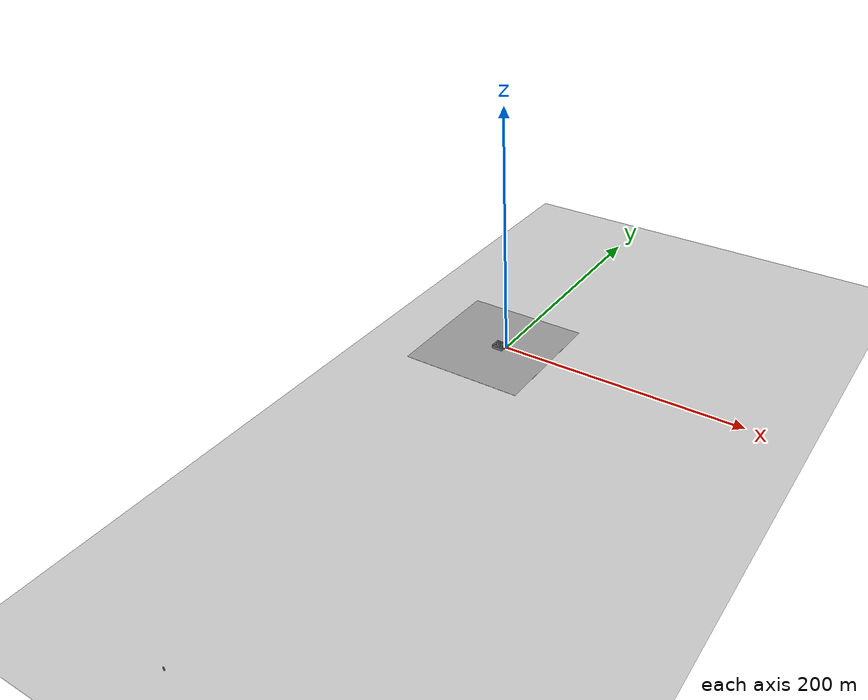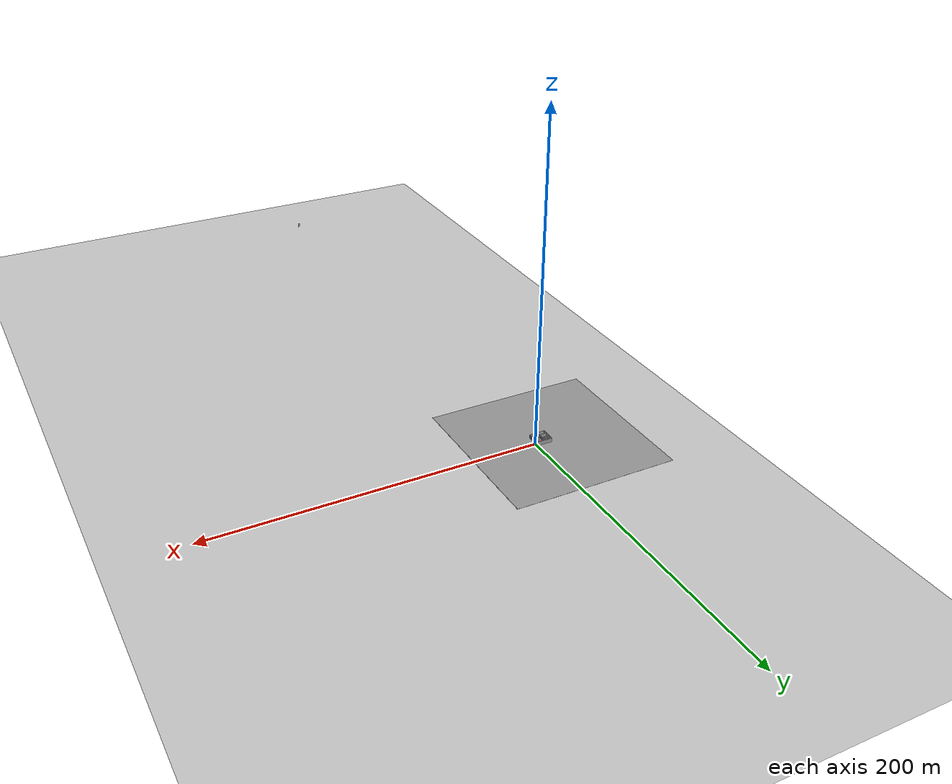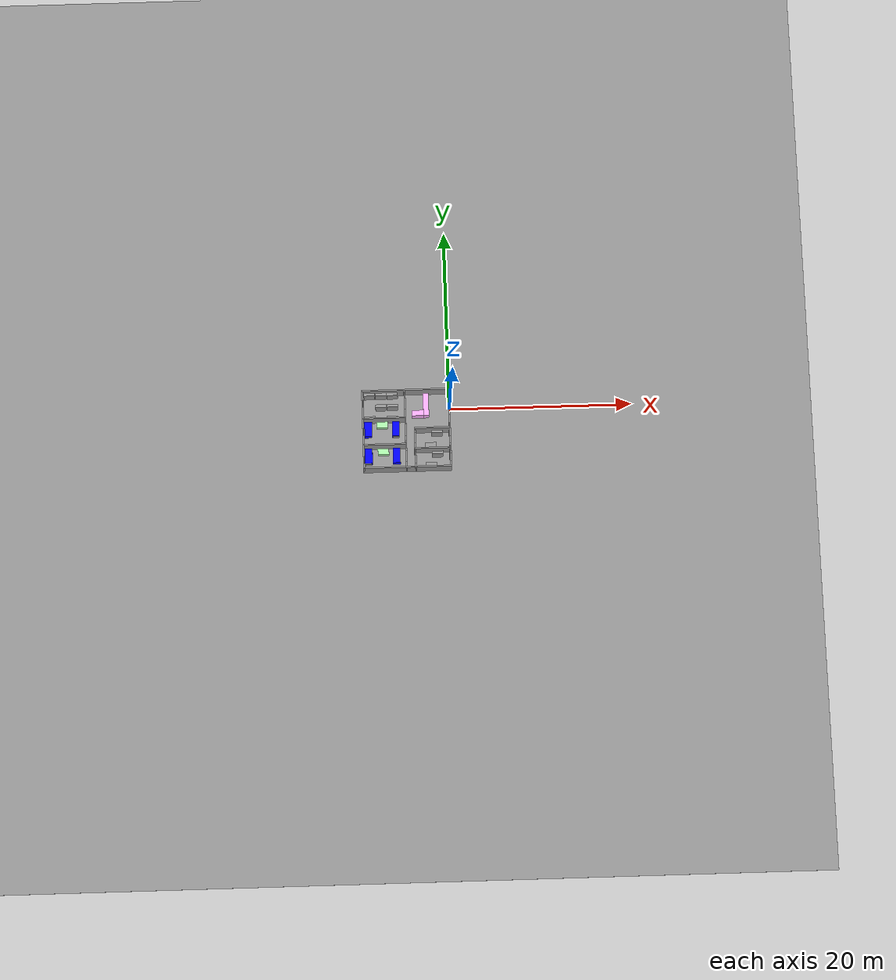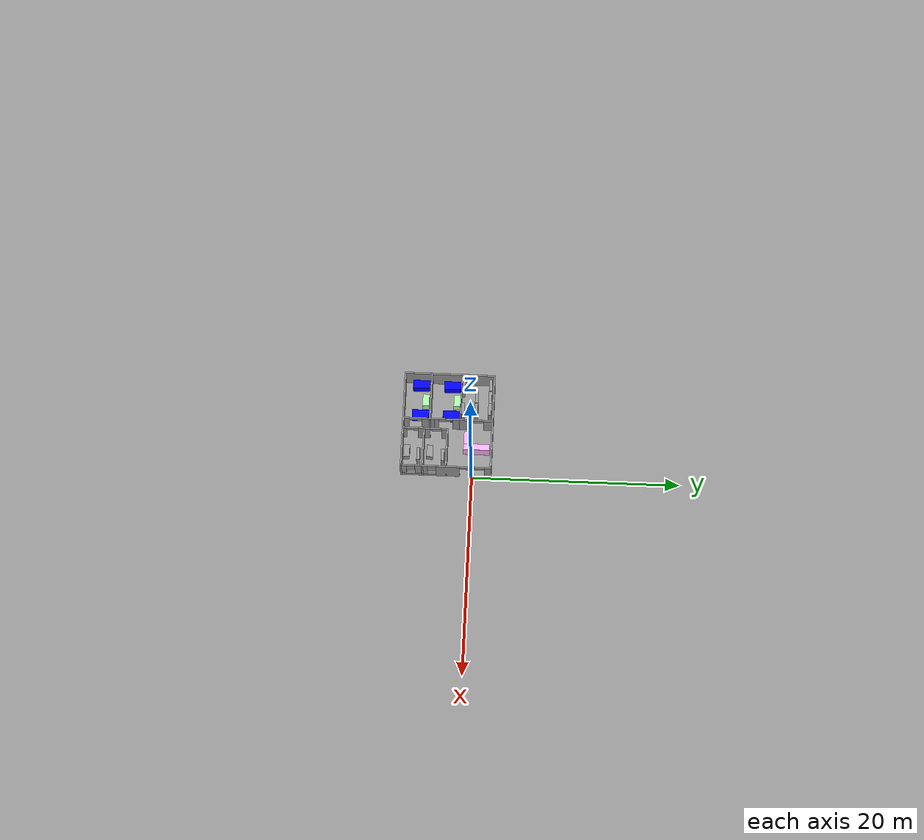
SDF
<sdf version="1.6">
 <world name="default">
  <light name="sun" type="directional">
   <pose>0 0 10 0 -0 0</pose>
   <diffuse>0.8 0.8 0.8 1</diffuse>
   <specular>0.2 0.2 0.2 1</specular>
   <attenuation>
    <range>1000</range>
    <constant>0.9</constant>
    <linear>0.01</linear>
    <quadratic>0.001</quadratic>
   </attenuation>
   <direction>-0.5 0.1 -0.9</direction>
  </light>
  <model name="ground_plane">
   <static>1</static>
   <link name="link">
    <collision name="collision">
     <geometry><plane><normal>0 0 1</normal><size>100 100</size></plane></geometry>
     <surface>
      <contact><collide_bitmask>65535</collide_bitmask></contact>
      <friction><ode><mu>100</mu><mu2>50</mu2></ode></friction>
     </surface>
    </collision>
    <visual name="visual">
     <cast_shadows>0</cast_shadows>
     <geometry><plane><normal>0 0 1</normal><size>100 100</size></plane></geometry>
     <material>
      <script><uri>file://media/materials/scripts/gazebo.material</uri><name>Gazebo/Grey</name></script>
     </material>
    </visual>
   </link>
  </model>
  <gravity>0 0 -9.8</gravity>
  <magnetic_field>6e-06 2.3e-05 -4.2e-05</magnetic_field>
  <atmosphere type="adiabatic"/>
  <physics name="default_physics" default="0" type="ode">
   <max_step_size>0.001</max_step_size>
   <real_time_factor>1</real_time_factor>
   <real_time_update_rate>1000</real_time_update_rate>
  </physics>
  <scene><ambient>0.4 0.4 0.4 1</ambient><background>0.7 0.7 0.7 1</background><shadows>1</shadows></scene>
  <audio><device>default</device></audio>
  <spherical_coordinates>
   <surface_model>EARTH_WGS84</surface_model>
   <latitude_deg>0</latitude_deg>
   <longitude_deg>0</longitude_deg>
   <elevation>0</elevation>
   <heading_deg>0</heading_deg>
  </spherical_coordinates>
  <model name="wall_real">
   <pose>-4.86138 -2.47863 0 0 -0 0</pose>
   <link name="Wall_0">
    <collision name="Wall_0_Collision">
     <geometry><box><size>3.25 0.15 2.5</size></box></geometry>
     <pose>0 0 1.25 0 -0 0</pose>
    </collision>
    <visual name="Wall_0_Visual">
     <pose>0 0 1.25 0 -0 0</pose>
     <geometry><box><size>3.25 0.15 2.5</size></box></geometry>
     <material>
      <script><uri>file://media/materials/scripts/gazebo.material</uri><name>Gazebo/Grey</name></script>
      <ambient>1 1 1 1</ambient>
     </material>
     <meta><layer>0</layer></meta>
    </visual>
    <pose>-4.75 2.75 0 0 -0 -1.5708</pose>
   </link>
   <link name="Wall_11">
    <collision name="Wall_11_Collision">
     <geometry><box><size>4 0.15 2.5</size></box></geometry>
     <pose>0 0 1.25 0 -0 0</pose>
    </collision>
    <visual name="Wall_11_Visual">
     <pose>0 0 1.25 0 -0 0</pose>
     <geometry><box><size>4 0.15 2.5</size></box></geometry>
     <material>
      <script><uri>file://media/materials/scripts/gazebo.material</uri><name>Gazebo/Grey</name></script>
      <ambient>1 1 1 1</ambient>
     </material>
     <meta><layer>0</layer></meta>
    </visual>
    <pose>2.825 -2.25 0 0 -0 3.14159</pose>
   </link>
   <link name="Wall_13">
    <pose>0.9 -1.125 0 0 -0 -1.5708</pose>
    <visual name="Wall_13_Visual_0">
     <pose>-0.890011 0 1.25 0 -0 0</pose>
     <geometry><box><size>0.619978 0.15 2.5</size></box></geometry>
     <material>
      <script><uri>file://media/materials/scripts/gazebo.material</uri><name>Gazebo/Grey</name></script>
      <ambient>1 1 1 1</ambient>
     </material>
     <meta><layer>0</layer></meta>
    </visual>
    <collision name="Wall_13_Collision_0">
     <geometry><box><size>0.619978 0.15 2.5</size></box></geometry>
     <pose>-0.890011 0 1.25 0 -0 0</pose>
    </collision>
    <visual name="Wall_13_Visual_1">
     <pose>0.873674 0 1.25 0 -0 0</pose>
     <geometry><box><size>0.652651 0.15 2.5</size></box></geometry>
     <material>
      <script><uri>file://media/materials/scripts/gazebo.material</uri><name>Gazebo/Grey</name></script>
      <ambient>1 1 1 1</ambient>
     </material>
     <meta><layer>0</layer></meta>
    </visual>
    <collision name="Wall_13_Collision_1">
     <geometry><box><size>0.652651 0.15 2.5</size></box></geometry>
     <pose>0.873674 0 1.25 0 -0 0</pose>
    </collision>
    <visual name="Wall_13_Visual_2">
     <pose>-0.016337 0 2.25 0 -0 0</pose>
     <geometry><box><size>1.12737 0.15 0.5</size></box></geometry>
     <material>
      <script><uri>file://media/materials/scripts/gazebo.material</uri><name>Gazebo/Grey</name></script>
      <ambient>1 1 1 1</ambient>
     </material>
     <meta><layer>0</layer></meta>
    </visual>
    <collision name="Wall_13_Collision_2">
     <geometry><box><size>1.12737 0.15 0.5</size></box></geometry>
     <pose>-0.016337 0 2.25 0 -0 0</pose>
    </collision>
   </link>
   <link name="Wall_14">
    <pose>0.9 -3.275 0 0 -0 -1.5708</pose>
    <visual name="Wall_14_Visual_0">
     <pose>-0.778157 0 1.25 0 -0 0</pose>
     <geometry><box><size>0.643686 0.15 2.5</size></box></geometry>
     <material>
      <script><uri>file://media/materials/scripts/gazebo.material</uri><name>Gazebo/Grey</name></script>
      <ambient>1 1 1 1</ambient>
     </material>
     <meta><layer>0</layer></meta>
    </visual>
    <collision name="Wall_14_Collision_0">
     <geometry><box><size>0.643686 0.15 2.5</size></box></geometry>
     <pose>-0.778157 0 1.25 0 -0 0</pose>
    </collision>
    <visual name="Wall_14_Visual_1">
     <pose>0.868038 0 1.25 0 -0 0</pose>
     <geometry><box><size>0.463923 0.15 2.5</size></box></geometry>
     <material>
      <script><uri>file://media/materials/scripts/gazebo.material</uri><name>Gazebo/Grey</name></script>
      <ambient>1 1 1 1</ambient>
     </material>
     <meta><layer>0</layer></meta>
    </visual>
    <collision name="Wall_14_Collision_1">
     <geometry><box><size>0.463923 0.15 2.5</size></box></geometry>
     <pose>0.868038 0 1.25 0 -0 0</pose>
    </collision>
    <visual name="Wall_14_Visual_2">
     <pose>0.089881 0 2.25 0 -0 0</pose>
     <geometry><box><size>1.09239 0.15 0.5</size></box></geometry>
     <material>
      <script><uri>file://media/materials/scripts/gazebo.material</uri><name>Gazebo/Grey</name></script>
      <ambient>1 1 1 1</ambient>
     </material>
     <meta><layer>0</layer></meta>
    </visual>
    <collision name="Wall_14_Collision_2">
     <geometry><box><size>1.09239 0.15 0.5</size></box></geometry>
     <pose>0.089881 0 2.25 0 -0 0</pose>
    </collision>
   </link>
   <link name="Wall_16">
    <pose>-0.1 -0.1 0 0 -0 -1.5708</pose>
    <visual name="Wall_16_Visual_0">
     <pose>-0.957502 0 1.25 0 -0 0</pose>
     <geometry><box><size>0.834995 0.15 2.5</size></box></geometry>
     <material>
      <script><uri>file://media/materials/scripts/gazebo.material</uri><name>Gazebo/Grey</name></script>
      <ambient>1 1 1 1</ambient>
     </material>
     <meta><layer>0</layer></meta>
    </visual>
    <collision name="Wall_16_Collision_0">
     <geometry><box><size>0.834995 0.15 2.5</size></box></geometry>
     <pose>-0.957502 0 1.25 0 -0 0</pose>
    </collision>
    <visual name="Wall_16_Visual_1">
     <pose>1.07681 0 1.25 0 -0 0</pose>
     <geometry><box><size>0.59638 0.15 2.5</size></box></geometry>
     <material>
      <script><uri>file://media/materials/scripts/gazebo.material</uri><name>Gazebo/Grey</name></script>
      <ambient>1 1 1 1</ambient>
     </material>
     <meta><layer>0</layer></meta>
    </visual>
    <collision name="Wall_16_Collision_1">
     <geometry><box><size>0.59638 0.15 2.5</size></box></geometry>
     <pose>1.07681 0 1.25 0 -0 0</pose>
    </collision>
    <visual name="Wall_16_Visual_2">
     <pose>0.119307 0 2.25 0 -0 0</pose>
     <geometry><box><size>1.31862 0.15 0.5</size></box></geometry>
     <material>
      <script><uri>file://media/materials/scripts/gazebo.material</uri><name>Gazebo/Grey</name></script>
      <ambient>1 1 1 1</ambient>
     </material>
     <meta><layer>0</layer></meta>
    </visual>
    <collision name="Wall_16_Collision_2">
     <geometry><box><size>1.31862 0.15 0.5</size></box></geometry>
     <pose>0.119307 0 2.25 0 -0 0</pose>
    </collision>
   </link>
   <link name="Wall_18">
    <pose>-0.1 -2.85 0 0 -0 -1.5708</pose>
    <visual name="Wall_18_Visual_0">
     <pose>-0.933477 0 1.25 0 -0 0</pose>
     <geometry><box><size>1.18305 0.15 2.5</size></box></geometry>
     <material>
      <script><uri>file://media/materials/scripts/gazebo.material</uri><name>Gazebo/Grey</name></script>
      <ambient>1 1 1 1</ambient>
     </material>
     <meta><layer>0</layer></meta>
    </visual>
    <collision name="Wall_18_Collision_0">
     <geometry><box><size>1.18305 0.15 2.5</size></box></geometry>
     <pose>-0.933477 0 1.25 0 -0 0</pose>
    </collision>
    <visual name="Wall_18_Visual_1">
     <pose>1.20344 0 1.25 0 -0 0</pose>
     <geometry><box><size>0.643126 0.15 2.5</size></box></geometry>
     <material>
      <script><uri>file://media/materials/scripts/gazebo.material</uri><name>Gazebo/Grey</name></script>
      <ambient>1 1 1 1</ambient>
     </material>
     <meta><layer>0</layer></meta>
    </visual>
    <collision name="Wall_18_Collision_1">
     <geometry><box><size>0.643126 0.15 2.5</size></box></geometry>
     <pose>1.20344 0 1.25 0 -0 0</pose>
    </collision>
    <visual name="Wall_18_Visual_2">
     <pose>0.26996 0 2.25 0 -0 0</pose>
     <geometry><box><size>1.22383 0.15 0.5</size></box></geometry>
     <material>
      <script><uri>file://media/materials/scripts/gazebo.material</uri><name>Gazebo/Grey</name></script>
      <ambient>1 1 1 1</ambient>
     </material>
     <meta><layer>0</layer></meta>
    </visual>
    <collision name="Wall_18_Collision_2">
     <geometry><box><size>1.22383 0.15 0.5</size></box></geometry>
     <pose>0.26996 0 2.25 0 -0 0</pose>
    </collision>
   </link>
   <link name="Wall_2">
    <collision name="Wall_2_Collision">
     <geometry><box><size>5.65 0.15 2.5</size></box></geometry>
     <pose>0 0 1.25 0 -0 0</pose>
    </collision>
    <visual name="Wall_2_Visual">
     <pose>0 0 1.25 0 -0 0</pose>
     <geometry><box><size>5.65 0.15 2.5</size></box></geometry>
     <material>
      <script><uri>file://media/materials/scripts/gazebo.material</uri><name>Gazebo/Grey</name></script>
      <ambient>1 1 1 1</ambient>
     </material>
     <meta><layer>0</layer></meta>
    </visual>
    <pose>-4.75 -1.55 0 0 -0 -1.5708</pose>
   </link>
   <link name="Wall_20">
    <collision name="Wall_20_Collision">
     <geometry><box><size>4.8 0.15 2.5</size></box></geometry>
     <pose>0 0 1.25 0 -0 0</pose>
    </collision>
    <visual name="Wall_20_Visual">
     <pose>0 0 1.25 0 -0 0</pose>
     <geometry><box><size>4.8 0.15 2.5</size></box></geometry>
     <material>
      <script><uri>file://media/materials/scripts/gazebo.material</uri><name>Gazebo/Grey</name></script>
      <ambient>1 1 1 1</ambient>
     </material>
     <meta><layer>0</layer></meta>
    </visual>
    <pose>-2.425 -1.72408 0 0 -0 3.14159</pose>
   </link>
   <link name="Wall_22">
    <pose>-0.1 2.75 0 0 -0 1.5708</pose>
    <visual name="Wall_22_Visual_0">
     <pose>-1.12521 0 1.25 0 -0 0</pose>
     <geometry><box><size>0.999582 0.15 2.5</size></box></geometry>
     <material>
      <script><uri>file://media/materials/scripts/gazebo.material</uri><name>Gazebo/Grey</name></script>
      <ambient>1 1 1 1</ambient>
     </material>
     <meta><layer>0</layer></meta>
    </visual>
    <collision name="Wall_22_Collision_0">
     <geometry><box><size>0.999582 0.15 2.5</size></box></geometry>
     <pose>-1.12521 0 1.25 0 -0 0</pose>
    </collision>
    <visual name="Wall_22_Visual_1">
     <pose>1.16953 0 1.25 0 -0 0</pose>
     <geometry><box><size>0.910936 0.15 2.5</size></box></geometry>
     <material>
      <script><uri>file://media/materials/scripts/gazebo.material</uri><name>Gazebo/Grey</name></script>
      <ambient>1 1 1 1</ambient>
     </material>
     <meta><layer>0</layer></meta>
    </visual>
    <collision name="Wall_22_Collision_1">
     <geometry><box><size>0.910936 0.15 2.5</size></box></geometry>
     <pose>1.16953 0 1.25 0 -0 0</pose>
    </collision>
    <visual name="Wall_22_Visual_2">
     <pose>0.044323 0 2.25 0 -0 0</pose>
     <geometry><box><size>1.33948 0.15 0.5</size></box></geometry>
     <material>
      <script><uri>file://media/materials/scripts/gazebo.material</uri><name>Gazebo/Grey</name></script>
      <ambient>1 1 1 1</ambient>
     </material>
     <meta><layer>0</layer></meta>
    </visual>
    <collision name="Wall_22_Collision_2">
     <geometry><box><size>1.33948 0.15 0.5</size></box></geometry>
     <pose>0.044323 0 2.25 0 -0 0</pose>
    </collision>
   </link>
   <link name="Wall_24">
    <collision name="Wall_24_Collision">
     <geometry><box><size>9.65 0.15 2.5</size></box></geometry>
     <pose>0 0 1.25 0 -0 0</pose>
    </collision>
    <visual name="Wall_24_Visual">
     <pose>0 0 1.25 0 -0 0</pose>
     <geometry><box><size>9.65 0.15 2.5</size></box></geometry>
     <material>
      <script><uri>file://media/materials/scripts/gazebo.material</uri><name>Gazebo/Grey</name></script>
      <ambient>1 1 1 1</ambient>
     </material>
     <meta><layer>0</layer></meta>
    </visual>
    <pose>-0 4.3 0 0 -0 0</pose>
   </link>
   <link name="Wall_26">
    <collision name="Wall_26_Collision">
     <geometry><box><size>9.65 0.15 2.5</size></box></geometry>
     <pose>0 0 1.25 0 -0 0</pose>
    </collision>
    <visual name="Wall_26_Visual">
     <pose>0 0 1.25 0 -0 0</pose>
     <geometry><box><size>9.65 0.15 2.5</size></box></geometry>
     <material>
      <script><uri>file://media/materials/scripts/gazebo.material</uri><name>Gazebo/Grey</name></script>
      <ambient>1 1 1 1</ambient>
     </material>
     <meta><layer>0</layer></meta>
    </visual>
    <pose>-0 -4.3 0 0 -0 0</pose>
   </link>
   <link name="Wall_4">
    <collision name="Wall_4_Collision">
     <geometry><box><size>4.75 0.1 2.5</size></box></geometry>
     <pose>0 0 1.25 0 -0 0</pose>
    </collision>
    <visual name="Wall_4_Visual">
     <pose>0 0 1.25 0 -0 0</pose>
     <geometry><box><size>4.75 0.1 2.5</size></box></geometry>
     <material>
      <script><uri>file://media/materials/scripts/gazebo.material</uri><name>Gazebo/Grey</name></script>
      <ambient>1 1 1 1</ambient>
     </material>
     <meta><layer>0</layer></meta>
    </visual>
    <pose>-2.425 1.2 0 0 -0 0</pose>
   </link>
   <link name="Wall_6">
    <pose>4.75 -0 0 0 -0 -1.5708</pose>
    <visual name="Wall_6_Visual_0">
     <pose>-4.03377 0 1.25 0 -0 0</pose>
     <geometry><box><size>0.682464 0.15 2.5</size></box></geometry>
     <material>
      <script><uri>file://media/materials/scripts/gazebo.material</uri><name>Gazebo/Grey</name></script>
      <ambient>1 1 1 1</ambient>
     </material>
     <meta><layer>0</layer></meta>
    </visual>
    <collision name="Wall_6_Collision_0">
     <geometry><box><size>0.682464 0.15 2.5</size></box></geometry>
     <pose>-4.03377 0 1.25 0 -0 0</pose>
    </collision>
    <visual name="Wall_6_Visual_1">
     <pose>-0.194728 0 1.25 0 -0 0</pose>
     <geometry><box><size>2.29234 0.15 2.5</size></box></geometry>
     <material>
      <script><uri>file://media/materials/scripts/gazebo.material</uri><name>Gazebo/Grey</name></script>
      <ambient>1 1 1 1</ambient>
     </material>
     <meta><layer>0</layer></meta>
    </visual>
    <collision name="Wall_6_Collision_1">
     <geometry><box><size>2.29234 0.15 2.5</size></box></geometry>
     <pose>-0.194728 0 1.25 0 -0 0</pose>
    </collision>
    <visual name="Wall_6_Visual_2">
     <pose>2.66322 0 0.25 0 -0 0</pose>
     <geometry><box><size>3.42356 0.15 0.5</size></box></geometry>
     <material>
      <script><uri>file://media/materials/scripts/gazebo.material</uri><name>Gazebo/Grey</name></script>
      <ambient>1 1 1 1</ambient>
     </material>
     <meta><layer>0</layer></meta>
    </visual>
    <collision name="Wall_6_Collision_2">
     <geometry><box><size>3.42356 0.15 0.5</size></box></geometry>
     <pose>2.66322 0 0.25 0 -0 0</pose>
    </collision>
    <visual name="Wall_6_Visual_3">
     <pose>2.34857 0 1.5 0 -0 0</pose>
     <geometry><box><size>1.19426 0.15 2</size></box></geometry>
     <material>
      <script><uri>file://media/materials/scripts/gazebo.material</uri><name>Gazebo/Grey</name></script>
      <ambient>1 1 1 1</ambient>
     </material>
     <meta><layer>0</layer></meta>
    </visual>
    <collision name="Wall_6_Collision_3">
     <geometry><box><size>1.19426 0.15 2</size></box></geometry>
     <pose>2.34857 0 1.5 0 -0 0</pose>
    </collision>
    <visual name="Wall_6_Visual_4">
     <pose>4.06035 0 1.5 0 -0 0</pose>
     <geometry><box><size>0.629299 0.15 2</size></box></geometry>
     <material>
      <script><uri>file://media/materials/scripts/gazebo.material</uri><name>Gazebo/Grey</name></script>
      <ambient>1 1 1 1</ambient>
     </material>
     <meta><layer>0</layer></meta>
    </visual>
    <collision name="Wall_6_Collision_4">
     <geometry><box><size>0.629299 0.15 2</size></box></geometry>
     <pose>4.06035 0 1.5 0 -0 0</pose>
    </collision>
    <visual name="Wall_6_Visual_5">
     <pose>1.35144 0 1.9 0 -0 0</pose>
     <geometry><box><size>0.8 0.15 1.2</size></box></geometry>
     <material>
      <script><uri>file://media/materials/scripts/gazebo.material</uri><name>Gazebo/Grey</name></script>
      <ambient>1 1 1 1</ambient>
     </material>
     <meta><layer>0</layer></meta>
    </visual>
    <collision name="Wall_6_Collision_5">
     <geometry><box><size>0.8 0.15 1.2</size></box></geometry>
     <pose>1.35144 0 1.9 0 -0 0</pose>
    </collision>
    <visual name="Wall_6_Visual_6">
     <pose>3.3457 0 1.9 0 -0 0</pose>
     <geometry><box><size>0.8 0.15 1.2</size></box></geometry>
     <material>
      <script><uri>file://media/materials/scripts/gazebo.material</uri><name>Gazebo/Grey</name></script>
      <ambient>1 1 1 1</ambient>
     </material>
     <meta><layer>0</layer></meta>
    </visual>
    <collision name="Wall_6_Collision_6">
     <geometry><box><size>0.8 0.15 1.2</size></box></geometry>
     <pose>3.3457 0 1.9 0 -0 0</pose>
    </collision>
    <visual name="Wall_6_Visual_7">
     <pose>-2.51672 0 2.25 0 -0 0</pose>
     <geometry><box><size>2.35164 0.15 0.5</size></box></geometry>
     <material>
      <script><uri>file://media/materials/scripts/gazebo.material</uri><name>Gazebo/Grey</name></script>
      <ambient>1 1 1 1</ambient>
     </material>
     <meta><layer>0</layer></meta>
    </visual>
    <collision name="Wall_6_Collision_7">
     <geometry><box><size>2.35164 0.15 0.5</size></box></geometry>
     <pose>-2.51672 0 2.25 0 -0 0</pose>
    </collision>
   </link>
   <link name="Wall_8">
    <collision name="Wall_8_Collision">
     <geometry><box><size>4 0.15 2.5</size></box></geometry>
     <pose>0 0 1.25 0 -0 0</pose>
    </collision>
    <visual name="Wall_8_Visual">
     <pose>0 0 1.25 0 -0 0</pose>
     <geometry><box><size>4 0.15 2.5</size></box></geometry>
     <material>
      <script><uri>file://media/materials/scripts/gazebo.material</uri><name>Gazebo/Grey</name></script>
      <ambient>1 1 1 1</ambient>
     </material>
     <meta><layer>0</layer></meta>
    </visual>
    <pose>2.825 -0 0 0 -0 3.14159</pose>
   </link>
   <static>1</static>
  </model>
  <model name="hospitalWithDecoration">
   <link name="link_0">
    <inertial>
     <mass>1.32038</mass>
     <inertia>
      <ixx>0.310098</ixx>
      <ixy>0</ixy>
      <ixz>0</ixz>
      <iyy>0.442519</iyy>
      <iyz>0</iyz>
      <izz>0.230475</izz>
     </inertia>
    </inertial>
    <pose>2.06742 16.2261 -0.004167 0 -0 0</pose>
    <visual name="visual">
     <geometry><box><size>1.3 0.6 1.4</size></box></geometry>
     <material>
      <lighting>1</lighting>
      <script><uri>file://media/materials/scripts/gazebo.material</uri><name>Gazebo/Grey</name></script>
      <shader type="pixel"><normal_map>__default__</normal_map></shader>
      <ambient>1 0 1 0</ambient>
      <diffuse>1 0.7 1 1</diffuse>
      <specular>0.01 0.01 0.01 1</specular>
      <emissive>0 0 0 1</emissive>
     </material>
    </visual>
    <collision name="collision">
     <geometry><box><size>1.3 0.6 1.4</size></box></geometry>
     <surface>
      <friction>
       <ode><mu>1</mu><mu2>1</mu2><fdir1>0 0 0</fdir1><slip1>0</slip1><slip2>0</slip2></ode>
       <torsional>
        <coefficient>1</coefficient>
        <patch_radius>0</patch_radius>
        <surface_radius>0</surface_radius>
        <use_patch_radius>1</use_patch_radius>
        <ode><slip>0</slip></ode>
       </torsional>
      </friction>
      <bounce><restitution_coefficient>0</restitution_coefficient><threshold>1e+06</threshold></bounce>
      <contact>
       <collide_without_contact>0</collide_without_contact>
       <collide_without_contact_bitmask>1</collide_without_contact_bitmask>
       <collide_bitmask>1</collide_bitmask>
       <ode>
        <soft_cfm>0</soft_cfm>
        <soft_erp>0.2</soft_erp>
        <kp>1e+13</kp>
        <kd>1</kd>
        <max_vel>0.01</max_vel>
        <min_depth>0</min_depth>
       </ode>
       <bullet>
        <split_impulse>1</split_impulse>
        <split_impulse_penetration_threshold>-0.01</split_impulse_penetration_threshold>
        <soft_cfm>0</soft_cfm>
        <soft_erp>0.2</soft_erp>
        <kp>1e+13</kp>
        <kd>1</kd>
       </bullet>
      </contact>
     </surface>
    </collision>
   </link>
   <link name="link_1">
    <inertial>
     <mass>2.44409</mass>
     <inertia><ixx>1.67216</ixx><ixy>0</ixy><ixz>0</ixz><iyy>0.472523</iyy><iyz>0</iyz><izz>1.34629</izz></inertia>
    </inertial>
    <pose>3.00267 17.171 -0.004167 0 -0 0</pose>
    <visual name="visual">
     <geometry><box><size>0.6 2.5 1.4</size></box></geometry>
     <material>
      <lighting>1</lighting>
      <script><uri>file://media/materials/scripts/gazebo.material</uri><name>Gazebo/Grey</name></script>
      <shader type="pixel"><normal_map>__default__</normal_map></shader>
      <ambient>1 0 1 0</ambient>
      <diffuse>1 0.7 1 1</diffuse>
      <specular>0.01 0.01 0.01 1</specular>
      <emissive>0 0 0 1</emissive>
     </material>
    </visual>
    <collision name="collision">
     <geometry><box><size>0.6 2.5 1.4</size></box></geometry>
     <surface>
      <friction>
       <ode><mu>1</mu><mu2>1</mu2><fdir1>0 0 0</fdir1><slip1>0</slip1><slip2>0</slip2></ode>
       <torsional>
        <coefficient>1</coefficient>
        <patch_radius>0</patch_radius>
        <surface_radius>0</surface_radius>
        <use_patch_radius>1</use_patch_radius>
        <ode><slip>0</slip></ode>
       </torsional>
      </friction>
      <bounce><restitution_coefficient>0</restitution_coefficient><threshold>1e+06</threshold></bounce>
      <contact>
       <collide_without_contact>0</collide_without_contact>
       <collide_without_contact_bitmask>1</collide_without_contact_bitmask>
       <collide_bitmask>1</collide_bitmask>
       <ode>
        <soft_cfm>0</soft_cfm>
        <soft_erp>0.2</soft_erp>
        <kp>1e+13</kp>
        <kd>1</kd>
        <max_vel>0.01</max_vel>
        <min_depth>0</min_depth>
       </ode>
       <bullet>
        <split_impulse>1</split_impulse>
        <split_impulse_penetration_threshold>-0.01</split_impulse_penetration_threshold>
        <soft_cfm>0</soft_cfm>
        <soft_erp>0.2</soft_erp>
        <kp>1e+13</kp>
        <kd>1</kd>
       </bullet>
      </contact>
     </surface>
    </collision>
   </link>
   <link name="link_2_clone_5">
    <inertial>
     <mass>0.91642</mass>
     <inertia>
      <ixx>0.320278</ixx>
      <ixy>0</ixy>
      <ixz>0</ixz>
      <iyy>0.418308</iyy>
      <iyz>0</iyz>
      <izz>0.120202</izz>
     </inertia>
    </inertial>
    <pose>-3.18674 18.3004 0.295833 0 -0 0</pose>
    <visual name="visual">
     <geometry><box><size>1.2 0.3 2</size></box></geometry>
     <material>
      <lighting>1</lighting>
      <script><uri>file://media/materials/scripts/gazebo.material</uri><name>Gazebo/Grey</name></script>
      <shader type="pixel"><normal_map>__default__</normal_map></shader>
      <ambient>0.3 0.3 0.3 1</ambient>
      <diffuse>0.7 0.7 0.7 1</diffuse>
      <specular>0.01 0.01 0.01 1</specular>
      <emissive>0 0 0 1</emissive>
     </material>
    </visual>
    <visual name="ModelPreview_0::link_2_clone_5::visual_1">
     <geometry><box><size>1.2 0.3 2</size></box></geometry>
     <material>
      <lighting>1</lighting>
      <script><uri>file://media/materials/scripts/gazebo.material</uri><name>Gazebo/Grey</name></script>
      <shader type="pixel"><normal_map>__default__</normal_map></shader>
      <ambient>0.3 0.3 0.3 1</ambient>
      <diffuse>0.7 0.7 0.7 1</diffuse>
      <specular>0.01 0.01 0.01 1</specular>
      <emissive>0 0 0 1</emissive>
     </material>
    </visual>
    <collision name="collision">
     <geometry><box><size>1.2 0.3 2</size></box></geometry>
     <surface>
      <friction>
       <ode><mu>1</mu><mu2>1</mu2><fdir1>0 0 0</fdir1><slip1>0</slip1><slip2>0</slip2></ode>
       <torsional>
        <coefficient>1</coefficient>
        <patch_radius>0</patch_radius>
        <surface_radius>0</surface_radius>
        <use_patch_radius>1</use_patch_radius>
        <ode><slip>0</slip></ode>
       </torsional>
      </friction>
      <bounce><restitution_coefficient>0</restitution_coefficient><threshold>1e+06</threshold></bounce>
      <contact>
       <collide_without_contact>0</collide_without_contact>
       <collide_without_contact_bitmask>1</collide_without_contact_bitmask>
       <collide_bitmask>1</collide_bitmask>
       <ode>
        <soft_cfm>0</soft_cfm>
        <soft_erp>0.2</soft_erp>
        <kp>1e+13</kp>
        <kd>1</kd>
        <max_vel>0.01</max_vel>
        <min_depth>0</min_depth>
       </ode>
       <bullet>
        <split_impulse>1</split_impulse>
        <split_impulse_penetration_threshold>-0.01</split_impulse_penetration_threshold>
        <soft_cfm>0</soft_cfm>
        <soft_erp>0.2</soft_erp>
        <kp>1e+13</kp>
        <kd>1</kd>
       </bullet>
      </contact>
     </surface>
    </collision>
   </link>
   <link name="link_2_clone_5_clone_0">
    <inertial>
     <mass>0.91642</mass>
     <inertia>
      <ixx>0.320278</ixx>
      <ixy>0</ixy>
      <ixz>0</ixz>
      <iyy>0.418308</iyy>
      <iyz>0</iyz>
      <izz>0.120202</izz>
     </inertia>
    </inertial>
    <pose>-1.93674 18.3004 0.295833 0 -0 0</pose>
    <visual name="visual">
     <geometry><box><size>1.2 0.3 2</size></box></geometry>
     <material>
      <lighting>1</lighting>
      <script><uri>file://media/materials/scripts/gazebo.material</uri><name>Gazebo/Grey</name></script>
      <shader type="pixel"><normal_map>__default__</normal_map></shader>
      <ambient>0.3 0.3 0.3 1</ambient>
      <diffuse>0.7 0.7 0.7 1</diffuse>
      <specular>0.01 0.01 0.01 1</specular>
      <emissive>0 0 0 1</emissive>
     </material>
    </visual>
    <visual name="visual_1">
     <geometry><box><size>1.2 0.3 2</size></box></geometry>
     <material>
      <lighting>1</lighting>
      <script><uri>file://media/materials/scripts/gazebo.material</uri><name>Gazebo/Grey</name></script>
      <shader type="pixel"><normal_map>__default__</normal_map></shader>
      <ambient>0.3 0.3 0.3 1</ambient>
      <diffuse>0.7 0.7 0.7 1</diffuse>
      <specular>0.01 0.01 0.01 1</specular>
      <emissive>0 0 0 1</emissive>
     </material>
    </visual>
    <collision name="collision">
     <geometry><box><size>1.2 0.3 2</size></box></geometry>
     <surface>
      <friction>
       <ode><mu>1</mu><mu2>1</mu2><fdir1>0 0 0</fdir1><slip1>0</slip1><slip2>0</slip2></ode>
       <torsional>
        <coefficient>1</coefficient>
        <patch_radius>0</patch_radius>
        <surface_radius>0</surface_radius>
        <use_patch_radius>1</use_patch_radius>
        <ode><slip>0</slip></ode>
       </torsional>
      </friction>
      <bounce><restitution_coefficient>0</restitution_coefficient><threshold>1e+06</threshold></bounce>
      <contact>
       <collide_without_contact>0</collide_without_contact>
       <collide_without_contact_bitmask>1</collide_without_contact_bitmask>
       <collide_bitmask>1</collide_bitmask>
       <ode>
        <soft_cfm>0</soft_cfm>
        <soft_erp>0.2</soft_erp>
        <kp>1e+13</kp>
        <kd>1</kd>
        <max_vel>0.01</max_vel>
        <min_depth>0</min_depth>
       </ode>
       <bullet>
        <split_impulse>1</split_impulse>
        <split_impulse_penetration_threshold>-0.01</split_impulse_penetration_threshold>
        <soft_cfm>0</soft_cfm>
        <soft_erp>0.2</soft_erp>
        <kp>1e+13</kp>
        <kd>1</kd>
       </bullet>
      </contact>
     </surface>
    </collision>
   </link>
   <link name="link_2_clone_5_clone_1">
    <inertial>
     <mass>0.91642</mass>
     <inertia>
      <ixx>0.320278</ixx>
      <ixy>0</ixy>
      <ixz>0</ixz>
      <iyy>0.418308</iyy>
      <iyz>0</iyz>
      <izz>0.120202</izz>
     </inertia>
    </inertial>
    <pose>-0.686741 18.3004 0.295833 0 -0 0</pose>
    <visual name="visual">
     <geometry><box><size>1.2 0.3 2</size></box></geometry>
     <material>
      <lighting>1</lighting>
      <script><uri>file://media/materials/scripts/gazebo.material</uri><name>Gazebo/Grey</name></script>
      <shader type="pixel"><normal_map>__default__</normal_map></shader>
      <ambient>0.3 0.3 0.3 1</ambient>
      <diffuse>0.7 0.7 0.7 1</diffuse>
      <specular>0.01 0.01 0.01 1</specular>
      <emissive>0 0 0 1</emissive>
     </material>
    </visual>
    <collision name="collision">
     <geometry><box><size>1.2 0.3 2</size></box></geometry>
     <surface>
      <friction>
       <ode><mu>1</mu><mu2>1</mu2><fdir1>0 0 0</fdir1><slip1>0</slip1><slip2>0</slip2></ode>
       <torsional>
        <coefficient>1</coefficient>
        <patch_radius>0</patch_radius>
        <surface_radius>0</surface_radius>
        <use_patch_radius>1</use_patch_radius>
        <ode><slip>0</slip></ode>
       </torsional>
      </friction>
      <bounce><restitution_coefficient>0</restitution_coefficient><threshold>1e+06</threshold></bounce>
      <contact>
       <collide_without_contact>0</collide_without_contact>
       <collide_without_contact_bitmask>1</collide_without_contact_bitmask>
       <collide_bitmask>1</collide_bitmask>
       <ode>
        <soft_cfm>0</soft_cfm>
        <soft_erp>0.2</soft_erp>
        <kp>1e+13</kp>
        <kd>1</kd>
        <max_vel>0.01</max_vel>
        <min_depth>0</min_depth>
       </ode>
       <bullet>
        <split_impulse>1</split_impulse>
        <split_impulse_penetration_threshold>-0.01</split_impulse_penetration_threshold>
        <soft_cfm>0</soft_cfm>
        <soft_erp>0.2</soft_erp>
        <kp>1e+13</kp>
        <kd>1</kd>
       </bullet>
      </contact>
     </surface>
    </collision>
   </link>
   <link name="link_2_clone_5_clone_2">
    <inertial>
     <mass>0.91642</mass>
     <inertia>
      <ixx>0.320278</ixx>
      <ixy>0</ixy>
      <ixz>0</ixz>
      <iyy>0.418308</iyy>
      <iyz>0</iyz>
      <izz>0.120202</izz>
     </inertia>
    </inertial>
    <pose>-0.686741 17.0004 0.295833 0 -0 0</pose>
    <visual name="visual_1">
     <geometry><box><size>1.2 0.3 2</size></box></geometry>
     <material>
      <lighting>1</lighting>
      <script><uri>file://media/materials/scripts/gazebo.material</uri><name>Gazebo/Grey</name></script>
      <shader type="pixel"><normal_map>__default__</normal_map></shader>
      <ambient>0.3 0.3 0.3 1</ambient>
      <diffuse>0.7 0.7 0.7 1</diffuse>
      <specular>0.01 0.01 0.01 1</specular>
      <emissive>0 0 0 1</emissive>
     </material>
    </visual>
    <visual name="visual">
     <geometry><box><size>1.2 0.3 2</size></box></geometry>
     <material>
      <lighting>1</lighting>
      <script><uri>file://media/materials/scripts/gazebo.material</uri><name>Gazebo/Grey</name></script>
      <shader type="pixel"><normal_map>__default__</normal_map></shader>
      <ambient>0.3 0.3 0.3 1</ambient>
      <diffuse>0.7 0.7 0.7 1</diffuse>
      <specular>0.01 0.01 0.01 1</specular>
      <emissive>0 0 0 1</emissive>
     </material>
    </visual>
    <collision name="collision">
     <geometry><box><size>1.2 0.3 2</size></box></geometry>
     <surface>
      <friction>
       <ode><mu>1</mu><mu2>1</mu2><fdir1>0 0 0</fdir1><slip1>0</slip1><slip2>0</slip2></ode>
       <torsional>
        <coefficient>1</coefficient>
        <patch_radius>0</patch_radius>
        <surface_radius>0</surface_radius>
        <use_patch_radius>1</use_patch_radius>
        <ode><slip>0</slip></ode>
       </torsional>
      </friction>
      <bounce><restitution_coefficient>0</restitution_coefficient><threshold>1e+06</threshold></bounce>
      <contact>
       <collide_without_contact>0</collide_without_contact>
       <collide_without_contact_bitmask>1</collide_without_contact_bitmask>
       <collide_bitmask>1</collide_bitmask>
       <ode>
        <soft_cfm>0</soft_cfm>
        <soft_erp>0.2</soft_erp>
        <kp>1e+13</kp>
        <kd>1</kd>
        <max_vel>0.01</max_vel>
        <min_depth>0</min_depth>
       </ode>
       <bullet>
        <split_impulse>1</split_impulse>
        <split_impulse_penetration_threshold>-0.01</split_impulse_penetration_threshold>
        <soft_cfm>0</soft_cfm>
        <soft_erp>0.2</soft_erp>
        <kp>1e+13</kp>
        <kd>1</kd>
       </bullet>
      </contact>
     </surface>
    </collision>
   </link>
   <link name="link_2_clone_5_clone_2_clone">
    <inertial>
     <mass>0.91642</mass>
     <inertia>
      <ixx>0.320278</ixx>
      <ixy>0</ixy>
      <ixz>0</ixz>
      <iyy>0.418308</iyy>
      <iyz>0</iyz>
      <izz>0.120202</izz>
     </inertia>
    </inertial>
    <pose>4.13354 13.9745 0.295833 0 -0 0</pose>
    <visual name="visual">
     <geometry><box><size>1.2 0.3 2</size></box></geometry>
     <material>
      <lighting>1</lighting>
      <script><uri>file://media/materials/scripts/gazebo.material</uri><name>Gazebo/Grey</name></script>
      <shader type="pixel"><normal_map>__default__</normal_map></shader>
      <ambient>0.3 0.3 0.3 1</ambient>
      <diffuse>0.7 0.7 0.7 1</diffuse>
      <specular>0.01 0.01 0.01 1</specular>
      <emissive>0 0 0 1</emissive>
     </material>
    </visual>
    <visual name="visual_1">
     <geometry><box><size>1.2 0.3 2</size></box></geometry>
     <material>
      <lighting>1</lighting>
      <script><uri>file://media/materials/scripts/gazebo.material</uri><name>Gazebo/Grey</name></script>
      <shader type="pixel"><normal_map>__default__</normal_map></shader>
      <ambient>0.3 0.3 0.3 1</ambient>
      <diffuse>0.7 0.7 0.7 1</diffuse>
      <specular>0.01 0.01 0.01 1</specular>
      <emissive>0 0 0 1</emissive>
     </material>
    </visual>
    <collision name="collision">
     <geometry><box><size>1.2 0.3 2</size></box></geometry>
     <surface>
      <friction>
       <ode><mu>1</mu><mu2>1</mu2><fdir1>0 0 0</fdir1><slip1>0</slip1><slip2>0</slip2></ode>
       <torsional>
        <coefficient>1</coefficient>
        <patch_radius>0</patch_radius>
        <surface_radius>0</surface_radius>
        <use_patch_radius>1</use_patch_radius>
        <ode><slip>0</slip></ode>
       </torsional>
      </friction>
      <bounce><restitution_coefficient>0</restitution_coefficient><threshold>1e+06</threshold></bounce>
      <contact>
       <collide_without_contact>0</collide_without_contact>
       <collide_without_contact_bitmask>1</collide_without_contact_bitmask>
       <collide_bitmask>1</collide_bitmask>
       <ode>
        <soft_cfm>0</soft_cfm>
        <soft_erp>0.2</soft_erp>
        <kp>1e+13</kp>
        <kd>1</kd>
        <max_vel>0.01</max_vel>
        <min_depth>0</min_depth>
       </ode>
       <bullet>
        <split_impulse>1</split_impulse>
        <split_impulse_penetration_threshold>-0.01</split_impulse_penetration_threshold>
        <soft_cfm>0</soft_cfm>
        <soft_erp>0.2</soft_erp>
        <kp>1e+13</kp>
        <kd>1</kd>
       </bullet>
      </contact>
     </surface>
    </collision>
   </link>
   <link name="link_2_clone_5_clone_2_clone_0">
    <inertial>
     <mass>0.91642</mass>
     <inertia>
      <ixx>0.320278</ixx>
      <ixy>0</ixy>
      <ixz>0</ixz>
      <iyy>0.418308</iyy>
      <iyz>0</iyz>
      <izz>0.120202</izz>
     </inertia>
    </inertial>
    <pose>4.12688 11.6246 0.295833 0 -0 0</pose>
    <visual name="visual_1">
     <geometry><box><size>1.2 0.3 2</size></box></geometry>
     <material>
      <lighting>1</lighting>
      <script><uri>file://media/materials/scripts/gazebo.material</uri><name>Gazebo/Grey</name></script>
      <shader type="pixel"><normal_map>__default__</normal_map></shader>
      <ambient>0.3 0.3 0.3 1</ambient>
      <diffuse>0.7 0.7 0.7 1</diffuse>
      <specular>0.01 0.01 0.01 1</specular>
      <emissive>0 0 0 1</emissive>
     </material>
    </visual>
    <visual name="visual">
     <geometry><box><size>1.2 0.3 2</size></box></geometry>
     <material>
      <lighting>1</lighting>
      <script><uri>file://media/materials/scripts/gazebo.material</uri><name>Gazebo/Grey</name></script>
      <shader type="pixel"><normal_map>__default__</normal_map></shader>
      <ambient>0.3 0.3 0.3 1</ambient>
      <diffuse>0.7 0.7 0.7 1</diffuse>
      <specular>0.01 0.01 0.01 1</specular>
      <emissive>0 0 0 1</emissive>
     </material>
    </visual>
    <collision name="collision">
     <geometry><box><size>1.2 0.3 2</size></box></geometry>
     <surface>
      <friction>
       <ode><mu>1</mu><mu2>1</mu2><fdir1>0 0 0</fdir1><slip1>0</slip1><slip2>0</slip2></ode>
       <torsional>
        <coefficient>1</coefficient>
        <patch_radius>0</patch_radius>
        <surface_radius>0</surface_radius>
        <use_patch_radius>1</use_patch_radius>
        <ode><slip>0</slip></ode>
       </torsional>
      </friction>
      <bounce><restitution_coefficient>0</restitution_coefficient><threshold>1e+06</threshold></bounce>
      <contact>
       <collide_without_contact>0</collide_without_contact>
       <collide_without_contact_bitmask>1</collide_without_contact_bitmask>
       <collide_bitmask>1</collide_bitmask>
       <ode>
        <soft_cfm>0</soft_cfm>
        <soft_erp>0.2</soft_erp>
        <kp>1e+13</kp>
        <kd>1</kd>
        <max_vel>0.01</max_vel>
        <min_depth>0</min_depth>
       </ode>
       <bullet>
        <split_impulse>1</split_impulse>
        <split_impulse_penetration_threshold>-0.01</split_impulse_penetration_threshold>
        <soft_cfm>0</soft_cfm>
        <soft_erp>0.2</soft_erp>
        <kp>1e+13</kp>
        <kd>1</kd>
       </bullet>
      </contact>
     </surface>
    </collision>
   </link>
   <link name="link_2_clone_5_clone_3">
    <inertial>
     <mass>0.91642</mass>
     <inertia>
      <ixx>0.320278</ixx>
      <ixy>0</ixy>
      <ixz>0</ixz>
      <iyy>0.418308</iyy>
      <iyz>0</iyz>
      <izz>0.120202</izz>
     </inertia>
    </inertial>
    <pose>-1.93674 17.0004 0.295833 0 -0 0</pose>
    <visual name="visual_1">
     <geometry><box><size>1.2 0.3 2</size></box></geometry>
     <material>
      <lighting>1</lighting>
      <script><uri>file://media/materials/scripts/gazebo.material</uri><name>Gazebo/Grey</name></script>
      <shader type="pixel"><normal_map>__default__</normal_map></shader>
      <ambient>0.3 0.3 0.3 1</ambient>
      <diffuse>0.7 0.7 0.7 1</diffuse>
      <specular>0.01 0.01 0.01 1</specular>
      <emissive>0 0 0 1</emissive>
     </material>
    </visual>
    <visual name="visual">
     <geometry><box><size>1.2 0.3 2</size></box></geometry>
     <material>
      <lighting>1</lighting>
      <script><uri>file://media/materials/scripts/gazebo.material</uri><name>Gazebo/Grey</name></script>
      <shader type="pixel"><normal_map>__default__</normal_map></shader>
      <ambient>0.3 0.3 0.3 1</ambient>
      <diffuse>0.7 0.7 0.7 1</diffuse>
      <specular>0.01 0.01 0.01 1</specular>
      <emissive>0 0 0 1</emissive>
     </material>
    </visual>
    <collision name="collision">
     <geometry><box><size>1.2 0.3 2</size></box></geometry>
     <surface>
      <friction>
       <ode><mu>1</mu><mu2>1</mu2><fdir1>0 0 0</fdir1><slip1>0</slip1><slip2>0</slip2></ode>
       <torsional>
        <coefficient>1</coefficient>
        <patch_radius>0</patch_radius>
        <surface_radius>0</surface_radius>
        <use_patch_radius>1</use_patch_radius>
        <ode><slip>0</slip></ode>
       </torsional>
      </friction>
      <bounce><restitution_coefficient>0</restitution_coefficient><threshold>1e+06</threshold></bounce>
      <contact>
       <collide_without_contact>0</collide_without_contact>
       <collide_without_contact_bitmask>1</collide_without_contact_bitmask>
       <collide_bitmask>1</collide_bitmask>
       <ode>
        <soft_cfm>0</soft_cfm>
        <soft_erp>0.2</soft_erp>
        <kp>1e+13</kp>
        <kd>1</kd>
        <max_vel>0.01</max_vel>
        <min_depth>0</min_depth>
       </ode>
       <bullet>
        <split_impulse>1</split_impulse>
        <split_impulse_penetration_threshold>-0.01</split_impulse_penetration_threshold>
        <soft_cfm>0</soft_cfm>
        <soft_erp>0.2</soft_erp>
        <kp>1e+13</kp>
        <kd>1</kd>
       </bullet>
      </contact>
     </surface>
    </collision>
   </link>
   <link name="link_2_clone_5_clone_4">
    <inertial>
     <mass>0.91642</mass>
     <inertia>
      <ixx>0.320278</ixx>
      <ixy>0</ixy>
      <ixz>0</ixz>
      <iyy>0.418308</iyy>
      <iyz>0</iyz>
      <izz>0.120202</izz>
     </inertia>
    </inertial>
    <pose>-0.686741 15.7004 0.295833 0 -0 0</pose>
    <visual name="visual">
     <geometry><box><size>1.2 0.3 2</size></box></geometry>
     <material>
      <lighting>1</lighting>
      <script><uri>file://media/materials/scripts/gazebo.material</uri><name>Gazebo/Grey</name></script>
      <shader type="pixel"><normal_map>__default__</normal_map></shader>
      <ambient>0.3 0.3 0.3 1</ambient>
      <diffuse>0.7 0.7 0.7 1</diffuse>
      <specular>0.01 0.01 0.01 1</specular>
      <emissive>0 0 0 1</emissive>
     </material>
    </visual>
    <visual name="visual_1">
     <geometry><box><size>1.2 0.3 2</size></box></geometry>
     <material>
      <lighting>1</lighting>
      <script><uri>file://media/materials/scripts/gazebo.material</uri><name>Gazebo/Grey</name></script>
      <shader type="pixel"><normal_map>__default__</normal_map></shader>
      <ambient>0.3 0.3 0.3 1</ambient>
      <diffuse>0.7 0.7 0.7 1</diffuse>
      <specular>0.01 0.01 0.01 1</specular>
      <emissive>0 0 0 1</emissive>
     </material>
    </visual>
    <collision name="collision">
     <geometry><box><size>1.2 0.3 2</size></box></geometry>
     <surface>
      <friction>
       <ode><mu>1</mu><mu2>1</mu2><fdir1>0 0 0</fdir1><slip1>0</slip1><slip2>0</slip2></ode>
       <torsional>
        <coefficient>1</coefficient>
        <patch_radius>0</patch_radius>
        <surface_radius>0</surface_radius>
        <use_patch_radius>1</use_patch_radius>
        <ode><slip>0</slip></ode>
       </torsional>
      </friction>
      <bounce><restitution_coefficient>0</restitution_coefficient><threshold>1e+06</threshold></bounce>
      <contact>
       <collide_without_contact>0</collide_without_contact>
       <collide_without_contact_bitmask>1</collide_without_contact_bitmask>
       <collide_bitmask>1</collide_bitmask>
       <ode>
        <soft_cfm>0</soft_cfm>
        <soft_erp>0.2</soft_erp>
        <kp>1e+13</kp>
        <kd>1</kd>
        <max_vel>0.01</max_vel>
        <min_depth>0</min_depth>
       </ode>
       <bullet>
        <split_impulse>1</split_impulse>
        <split_impulse_penetration_threshold>-0.01</split_impulse_penetration_threshold>
        <soft_cfm>0</soft_cfm>
        <soft_erp>0.2</soft_erp>
        <kp>1e+13</kp>
        <kd>1</kd>
       </bullet>
      </contact>
     </surface>
    </collision>
   </link>
   <link name="link_2_clone_5_clone_6">
    <inertial>
     <mass>0.91642</mass>
     <inertia>
      <ixx>0.320278</ixx>
      <ixy>0</ixy>
      <ixz>0</ixz>
      <iyy>0.418308</iyy>
      <iyz>0</iyz>
      <izz>0.120202</izz>
     </inertia>
    </inertial>
    <pose>-3.18674 15.7004 0.295833 0 -0 0</pose>
    <visual name="visual">
     <geometry><box><size>1.2 0.3 2</size></box></geometry>
     <material>
      <lighting>1</lighting>
      <script><uri>file://media/materials/scripts/gazebo.material</uri><name>Gazebo/Grey</name></script>
      <shader type="pixel"><normal_map>__default__</normal_map></shader>
      <ambient>0.3 0.3 0.3 1</ambient>
      <diffuse>0.7 0.7 0.7 1</diffuse>
      <specular>0.01 0.01 0.01 1</specular>
      <emissive>0 0 0 1</emissive>
     </material>
    </visual>
    <visual name="visual_1">
     <geometry><box><size>1.2 0.3 2</size></box></geometry>
     <material>
      <lighting>1</lighting>
      <script><uri>file://media/materials/scripts/gazebo.material</uri><name>Gazebo/Grey</name></script>
      <shader type="pixel"><normal_map>__default__</normal_map></shader>
      <ambient>0.3 0.3 0.3 1</ambient>
      <diffuse>0.7 0.7 0.7 1</diffuse>
      <specular>0.01 0.01 0.01 1</specular>
      <emissive>0 0 0 1</emissive>
     </material>
    </visual>
    <collision name="collision">
     <geometry><box><size>1.2 0.3 2</size></box></geometry>
     <surface>
      <friction>
       <ode><mu>1</mu><mu2>1</mu2><fdir1>0 0 0</fdir1><slip1>0</slip1><slip2>0</slip2></ode>
       <torsional>
        <coefficient>1</coefficient>
        <patch_radius>0</patch_radius>
        <surface_radius>0</surface_radius>
        <use_patch_radius>1</use_patch_radius>
        <ode><slip>0</slip></ode>
       </torsional>
      </friction>
      <bounce><restitution_coefficient>0</restitution_coefficient><threshold>1e+06</threshold></bounce>
      <contact>
       <collide_without_contact>0</collide_without_contact>
       <collide_without_contact_bitmask>1</collide_without_contact_bitmask>
       <collide_bitmask>1</collide_bitmask>
       <ode>
        <soft_cfm>0</soft_cfm>
        <soft_erp>0.2</soft_erp>
        <kp>1e+13</kp>
        <kd>1</kd>
        <max_vel>0.01</max_vel>
        <min_depth>0</min_depth>
       </ode>
       <bullet>
        <split_impulse>1</split_impulse>
        <split_impulse_penetration_threshold>-0.01</split_impulse_penetration_threshold>
        <soft_cfm>0</soft_cfm>
        <soft_erp>0.2</soft_erp>
        <kp>1e+13</kp>
        <kd>1</kd>
       </bullet>
      </contact>
     </surface>
    </collision>
   </link>
   <link name="link_2_clone_clone_0">
    <inertial>
     <mass>1.6162</mass>
     <inertia><ixx>1.71556</ixx><ixy>0</ixy><ixz>0</ixz><iyy>1.88844</iyy><iyz>0</iyz><izz>0.211988</izz></inertia>
    </inertial>
    <pose>13.5476 -339.253 -0.204167 0 -0 0</pose>
    <visual name="visual">
     <geometry><box><size>1.19533 0.380996 3.5486</size></box></geometry>
     <material>
      <lighting>1</lighting>
      <script><uri>file://media/materials/scripts/gazebo.material</uri><name>Gazebo/Grey</name></script>
      <shader type="pixel"/>
     </material>
    </visual>
    <collision name="collision">
     <geometry><box><size>1.19533 0.380996 3.5486</size></box></geometry>
     <surface>
      <friction>
       <ode><mu>1</mu><mu2>1</mu2><fdir1>0 0 0</fdir1><slip1>0</slip1><slip2>0</slip2></ode>
       <torsional>
        <coefficient>1</coefficient>
        <patch_radius>0</patch_radius>
        <surface_radius>0</surface_radius>
        <use_patch_radius>1</use_patch_radius>
        <ode><slip>0</slip></ode>
       </torsional>
      </friction>
      <bounce><restitution_coefficient>0</restitution_coefficient><threshold>1e+06</threshold></bounce>
      <contact>
       <collide_without_contact>0</collide_without_contact>
       <collide_without_contact_bitmask>1</collide_without_contact_bitmask>
       <collide_bitmask>1</collide_bitmask>
       <ode>
        <soft_cfm>0</soft_cfm>
        <soft_erp>0.2</soft_erp>
        <kp>1e+13</kp>
        <kd>1</kd>
        <max_vel>0.01</max_vel>
        <min_depth>0</min_depth>
       </ode>
       <bullet>
        <split_impulse>1</split_impulse>
        <split_impulse_penetration_threshold>-0.01</split_impulse_penetration_threshold>
        <soft_cfm>0</soft_cfm>
        <soft_erp>0.2</soft_erp>
        <kp>1e+13</kp>
        <kd>1</kd>
       </bullet>
      </contact>
     </surface>
    </collision>
   </link>
   <link name="link_2_clone_clone_clone_0_clone">
    <inertial>
     <mass>684.4</mass>
     <inertia><ixx>185.873</ixx><ixy>0</ixy><ixz>0</ixz><iyy>50.6679</iyy><iyz>0</iyz><izz>191.332</izz></inertia>
    </inertial>
    <pose>-3.46295 11.5811 -0.204167 0 -0 0</pose>
    <visual name="visual">
     <geometry><box><size>0.701464 1.69195 0.629555</size></box></geometry>
     <material>
      <lighting>1</lighting>
      <script><uri>file://media/materials/scripts/gazebo.material</uri><name>Gazebo/Grey</name></script>
      <shader type="pixel"><normal_map>__default__</normal_map></shader>
      <ambient>0.3 0.3 0.3 1</ambient>
      <diffuse>0.7 0.7 0.7 1</diffuse>
      <specular>0.01 0.01 0.01 1</specular>
      <emissive>0 0 0 1</emissive>
     </material>
    </visual>
    <collision name="collision">
     <geometry><box><size>0.701464 1.69195 0.629555</size></box></geometry>
     <surface>
      <friction>
       <ode><mu>1</mu><mu2>1</mu2><fdir1>0 0 0</fdir1><slip1>0</slip1><slip2>0</slip2></ode>
       <torsional>
        <coefficient>1</coefficient>
        <patch_radius>0</patch_radius>
        <surface_radius>0</surface_radius>
        <use_patch_radius>1</use_patch_radius>
        <ode><slip>0</slip></ode>
       </torsional>
      </friction>
      <bounce><restitution_coefficient>0</restitution_coefficient><threshold>1e+06</threshold></bounce>
      <contact>
       <collide_without_contact>0</collide_without_contact>
       <collide_without_contact_bitmask>1</collide_without_contact_bitmask>
       <collide_bitmask>1</collide_bitmask>
       <ode>
        <soft_cfm>0</soft_cfm>
        <soft_erp>0.2</soft_erp>
        <kp>1e+13</kp>
        <kd>1</kd>
        <max_vel>0.01</max_vel>
        <min_depth>0</min_depth>
       </ode>
       <bullet>
        <split_impulse>1</split_impulse>
        <split_impulse_penetration_threshold>-0.01</split_impulse_penetration_threshold>
        <soft_cfm>0</soft_cfm>
        <soft_erp>0.2</soft_erp>
        <kp>1e+13</kp>
        <kd>1</kd>
       </bullet>
      </contact>
     </surface>
    </collision>
   </link>
   <link name="link_2_clone_clone_clone_0_clone_0">
    <inertial>
     <mass>684.4</mass>
     <inertia><ixx>185.873</ixx><ixy>0</ixy><ixz>0</ixz><iyy>50.6679</iyy><iyz>0</iyz><izz>191.332</izz></inertia>
    </inertial>
    <pose>-0.320598 14.6198 -0.204167 0 -0 0</pose>
    <visual name="visual">
     <geometry><box><size>0.701464 1.69195 0.629555</size></box></geometry>
     <material>
      <lighting>1</lighting>
      <script><uri>file://media/materials/scripts/gazebo.material</uri><name>Gazebo/Grey</name></script>
      <shader type="pixel"><normal_map>__default__</normal_map></shader>
      <ambient>0.3 0.3 0.3 1</ambient>
      <diffuse>0.7 0.7 0.7 1</diffuse>
      <specular>0.01 0.01 0.01 1</specular>
      <emissive>0 0 0 1</emissive>
     </material>
    </visual>
    <collision name="collision">
     <geometry><box><size>0.701464 1.69195 0.629555</size></box></geometry>
     <surface>
      <friction>
       <ode><mu>1</mu><mu2>1</mu2><fdir1>0 0 0</fdir1><slip1>0</slip1><slip2>0</slip2></ode>
       <torsional>
        <coefficient>1</coefficient>
        <patch_radius>0</patch_radius>
        <surface_radius>0</surface_radius>
        <use_patch_radius>1</use_patch_radius>
        <ode><slip>0</slip></ode>
       </torsional>
      </friction>
      <bounce><restitution_coefficient>0</restitution_coefficient><threshold>1e+06</threshold></bounce>
      <contact>
       <collide_without_contact>0</collide_without_contact>
       <collide_without_contact_bitmask>1</collide_without_contact_bitmask>
       <collide_bitmask>1</collide_bitmask>
       <ode>
        <soft_cfm>0</soft_cfm>
        <soft_erp>0.2</soft_erp>
        <kp>1e+13</kp>
        <kd>1</kd>
        <max_vel>0.01</max_vel>
        <min_depth>0</min_depth>
       </ode>
       <bullet>
        <split_impulse>1</split_impulse>
        <split_impulse_penetration_threshold>-0.01</split_impulse_penetration_threshold>
        <soft_cfm>0</soft_cfm>
        <soft_erp>0.2</soft_erp>
        <kp>1e+13</kp>
        <kd>1</kd>
       </bullet>
      </contact>
     </surface>
    </collision>
   </link>
   <link name="link_2_clone_clone_clone_clone">
    <inertial>
     <mass>0.681721</mass>
     <inertia>
      <ixx>0.0688216</ixx>
      <ixy>0</ixy>
      <ixz>0</ixz>
      <iyy>0.127179</iyy>
      <iyz>0</iyz>
      <izz>0.103985</izz>
     </inertia>
    </inertial>
    <pose>-1.85518 15.1059 -0.204167 0 -0 0</pose>
    <visual name="visual">
     <geometry><box><size>1.19533 0.633707 0.899916</size></box></geometry>
     <material>
      <lighting>1</lighting>
      <script><uri>file://media/materials/scripts/gazebo.material</uri><name>Gazebo/Grey</name></script>
      <shader type="pixel"><normal_map>__default__</normal_map></shader>
      <ambient>0 1 0 0</ambient>
      <diffuse>0.7 1 0.7 1</diffuse>
      <specular>0.01 0.01 0.01 1</specular>
      <emissive>0 0 0 1</emissive>
     </material>
    </visual>
    <collision name="collision">
     <geometry><box><size>1.19533 0.633707 0.899916</size></box></geometry>
     <surface>
      <friction>
       <ode><mu>1</mu><mu2>1</mu2><fdir1>0 0 0</fdir1><slip1>0</slip1><slip2>0</slip2></ode>
       <torsional>
        <coefficient>1</coefficient>
        <patch_radius>0</patch_radius>
        <surface_radius>0</surface_radius>
        <use_patch_radius>1</use_patch_radius>
        <ode><slip>0</slip></ode>
       </torsional>
      </friction>
      <bounce><restitution_coefficient>0</restitution_coefficient><threshold>1e+06</threshold></bounce>
      <contact>
       <collide_without_contact>0</collide_without_contact>
       <collide_without_contact_bitmask>1</collide_without_contact_bitmask>
       <collide_bitmask>1</collide_bitmask>
       <ode>
        <soft_cfm>0</soft_cfm>
        <soft_erp>0.2</soft_erp>
        <kp>1e+13</kp>
        <kd>1</kd>
        <max_vel>0.01</max_vel>
        <min_depth>0</min_depth>
       </ode>
       <bullet>
        <split_impulse>1</split_impulse>
        <split_impulse_penetration_threshold>-0.01</split_impulse_penetration_threshold>
        <soft_cfm>0</soft_cfm>
        <soft_erp>0.2</soft_erp>
        <kp>1e+13</kp>
        <kd>1</kd>
       </bullet>
      </contact>
     </surface>
    </collision>
   </link>
   <link name="link_2_clone_clone_clone_clone_clone">
    <inertial>
     <mass>0.681721</mass>
     <inertia>
      <ixx>0.0688216</ixx>
      <ixy>0</ixy>
      <ixz>0</ixz>
      <iyy>0.127179</iyy>
      <iyz>0</iyz>
      <izz>0.103985</izz>
     </inertia>
    </inertial>
    <pose>3.4405 10.4529 -0.204167 0 -0 0</pose>
    <visual name="visual">
     <geometry><box><size>1.2 0.6 0.8</size></box></geometry>
     <material>
      <lighting>1</lighting>
      <script><uri>file://media/materials/scripts/gazebo.material</uri><name>Gazebo/Grey</name></script>
      <shader type="pixel"><normal_map>__default__</normal_map></shader>
      <ambient>0.3 0.3 0.3 1</ambient>
      <diffuse>0.7 0.7 0.7 1</diffuse>
      <specular>0.01 0.01 0.01 1</specular>
      <emissive>0 0 0 1</emissive>
     </material>
    </visual>
    <collision name="collision">
     <geometry><box><size>1.2 0.6 0.8</size></box></geometry>
     <surface>
      <friction>
       <ode><mu>1</mu><mu2>1</mu2><fdir1>0 0 0</fdir1><slip1>0</slip1><slip2>0</slip2></ode>
       <torsional>
        <coefficient>1</coefficient>
        <patch_radius>0</patch_radius>
        <surface_radius>0</surface_radius>
        <use_patch_radius>1</use_patch_radius>
        <ode><slip>0</slip></ode>
       </torsional>
      </friction>
      <bounce><restitution_coefficient>0</restitution_coefficient><threshold>1e+06</threshold></bounce>
      <contact>
       <collide_without_contact>0</collide_without_contact>
       <collide_without_contact_bitmask>1</collide_without_contact_bitmask>
       <collide_bitmask>1</collide_bitmask>
       <ode>
        <soft_cfm>0</soft_cfm>
        <soft_erp>0.2</soft_erp>
        <kp>1e+13</kp>
        <kd>1</kd>
        <max_vel>0.01</max_vel>
        <min_depth>0</min_depth>
       </ode>
       <bullet>
        <split_impulse>1</split_impulse>
        <split_impulse_penetration_threshold>-0.01</split_impulse_penetration_threshold>
        <soft_cfm>0</soft_cfm>
        <soft_erp>0.2</soft_erp>
        <kp>1e+13</kp>
        <kd>1</kd>
       </bullet>
      </contact>
     </surface>
    </collision>
   </link>
   <link name="link_2_clone_clone_clone_clone_clone_0">
    <inertial>
     <mass>0.681721</mass>
     <inertia>
      <ixx>0.0688216</ixx>
      <ixy>0</ixy>
      <ixz>0</ixz>
      <iyy>0.127179</iyy>
      <iyz>0</iyz>
      <izz>0.103985</izz>
     </inertia>
    </inertial>
    <pose>-1.81148 12.0932 -0.204167 0 -0 0</pose>
    <visual name="visual">
     <geometry><box><size>1.19533 0.633707 0.899916</size></box></geometry>
     <material>
      <lighting>1</lighting>
      <script><uri>file://media/materials/scripts/gazebo.material</uri><name>Gazebo/Grey</name></script>
      <shader type="pixel"><normal_map>__default__</normal_map></shader>
      <ambient>0 1 0 0</ambient>
      <diffuse>0.7 1 0.7 1</diffuse>
      <specular>0.01 0.01 0.01 1</specular>
      <emissive>0 0 0 1</emissive>
     </material>
    </visual>
    <collision name="collision">
     <geometry><box><size>1.19533 0.633707 0.899916</size></box></geometry>
     <surface>
      <friction>
       <ode><mu>1</mu><mu2>1</mu2><fdir1>0 0 0</fdir1><slip1>0</slip1><slip2>0</slip2></ode>
       <torsional>
        <coefficient>1</coefficient>
        <patch_radius>0</patch_radius>
        <surface_radius>0</surface_radius>
        <use_patch_radius>1</use_patch_radius>
        <ode><slip>0</slip></ode>
       </torsional>
      </friction>
      <bounce><restitution_coefficient>0</restitution_coefficient><threshold>1e+06</threshold></bounce>
      <contact>
       <collide_without_contact>0</collide_without_contact>
       <collide_without_contact_bitmask>1</collide_without_contact_bitmask>
       <collide_bitmask>1</collide_bitmask>
       <ode>
        <soft_cfm>0</soft_cfm>
        <soft_erp>0.2</soft_erp>
        <kp>1e+13</kp>
        <kd>1</kd>
        <max_vel>0.01</max_vel>
        <min_depth>0</min_depth>
       </ode>
       <bullet>
        <split_impulse>1</split_impulse>
        <split_impulse_penetration_threshold>-0.01</split_impulse_penetration_threshold>
        <soft_cfm>0</soft_cfm>
        <soft_erp>0.2</soft_erp>
        <kp>1e+13</kp>
        <kd>1</kd>
       </bullet>
      </contact>
     </surface>
    </collision>
   </link>
   <link name="link_2_clone_clone_clone_clone_clone_clone">
    <inertial>
     <mass>0.681721</mass>
     <inertia>
      <ixx>0.0688216</ixx>
      <ixy>0</ixy>
      <ixz>0</ixz>
      <iyy>0.127179</iyy>
      <iyz>0</iyz>
      <izz>0.103985</izz>
     </inertia>
    </inertial>
    <pose>3.39587 12.6892 -0.204167 0 -0 0</pose>
    <visual name="visual">
     <geometry><box><size>1.2 0.6 0.8</size></box></geometry>
     <material>
      <lighting>1</lighting>
      <script><uri>file://media/materials/scripts/gazebo.material</uri><name>Gazebo/Grey</name></script>
      <shader type="pixel"><normal_map>__default__</normal_map></shader>
      <ambient>0.3 0.3 0.3 1</ambient>
      <diffuse>0.7 0.7 0.7 1</diffuse>
      <specular>0.01 0.01 0.01 1</specular>
      <emissive>0 0 0 1</emissive>
     </material>
    </visual>
    <collision name="collision">
     <geometry><box><size>1.2 0.6 0.8</size></box></geometry>
     <surface>
      <friction>
       <ode><mu>1</mu><mu2>1</mu2><fdir1>0 0 0</fdir1><slip1>0</slip1><slip2>0</slip2></ode>
       <torsional>
        <coefficient>1</coefficient>
        <patch_radius>0</patch_radius>
        <surface_radius>0</surface_radius>
        <use_patch_radius>1</use_patch_radius>
        <ode><slip>0</slip></ode>
       </torsional>
      </friction>
      <bounce><restitution_coefficient>0</restitution_coefficient><threshold>1e+06</threshold></bounce>
      <contact>
       <collide_without_contact>0</collide_without_contact>
       <collide_without_contact_bitmask>1</collide_without_contact_bitmask>
       <collide_bitmask>1</collide_bitmask>
       <ode>
        <soft_cfm>0</soft_cfm>
        <soft_erp>0.2</soft_erp>
        <kp>1e+13</kp>
        <kd>1</kd>
        <max_vel>0.01</max_vel>
        <min_depth>0</min_depth>
       </ode>
       <bullet>
        <split_impulse>1</split_impulse>
        <split_impulse_penetration_threshold>-0.01</split_impulse_penetration_threshold>
        <soft_cfm>0</soft_cfm>
        <soft_erp>0.2</soft_erp>
        <kp>1e+13</kp>
        <kd>1</kd>
       </bullet>
      </contact>
     </surface>
    </collision>
   </link>
   <link name="link_3">
    <inertial>
     <mass>1</mass>
     <inertia>
      <ixx>0.166667</ixx>
      <ixy>0</ixy>
      <ixz>0</ixz>
      <iyy>0.166667</iyy>
      <iyz>0</iyz>
      <izz>0.166667</izz>
     </inertia>
    </inertial>
    <pose>-0.370451 14.6192 -0.204167 0 -0 0</pose>
    <visual name="visual">
     <geometry><box><size>0.8 1.6 1</size></box></geometry>
     <material>
      <lighting>1</lighting>
      <script><uri>file://media/materials/scripts/gazebo.material</uri><name>Gazebo/Grey</name></script>
      <shader type="pixel"><normal_map>__default__</normal_map></shader>
      <ambient>0 0 1 1</ambient>
      <diffuse>0 0 1 1</diffuse>
      <specular>0.01 0.01 0.01 1</specular>
      <emissive>0 0 0 1</emissive>
     </material>
    </visual>
    <collision name="collision">
     <geometry><box><size>0.8 1.6 1</size></box></geometry>
     <surface>
      <friction>
       <ode><mu>1</mu><mu2>1</mu2><fdir1>0 0 0</fdir1><slip1>0</slip1><slip2>0</slip2></ode>
       <torsional>
        <coefficient>1</coefficient>
        <patch_radius>0</patch_radius>
        <surface_radius>0</surface_radius>
        <use_patch_radius>1</use_patch_radius>
        <ode><slip>0</slip></ode>
       </torsional>
      </friction>
      <bounce><restitution_coefficient>0</restitution_coefficient><threshold>1e+06</threshold></bounce>
      <contact>
       <collide_without_contact>0</collide_without_contact>
       <collide_without_contact_bitmask>1</collide_without_contact_bitmask>
       <collide_bitmask>1</collide_bitmask>
       <ode>
        <soft_cfm>0</soft_cfm>
        <soft_erp>0.2</soft_erp>
        <kp>1e+13</kp>
        <kd>1</kd>
        <max_vel>0.01</max_vel>
        <min_depth>0</min_depth>
       </ode>
       <bullet>
        <split_impulse>1</split_impulse>
        <split_impulse_penetration_threshold>-0.01</split_impulse_penetration_threshold>
        <soft_cfm>0</soft_cfm>
        <soft_erp>0.2</soft_erp>
        <kp>1e+13</kp>
        <kd>1</kd>
       </bullet>
      </contact>
     </surface>
    </collision>
   </link>
   <link name="link_3_clone">
    <inertial>
     <mass>1</mass>
     <inertia>
      <ixx>0.166667</ixx>
      <ixy>0</ixy>
      <ixz>0</ixz>
      <iyy>0.166667</iyy>
      <iyz>0</iyz>
      <izz>0.166667</izz>
     </inertia>
    </inertial>
    <pose>-0.362505 11.6227 -0.204167 0 -0 0</pose>
    <visual name="visual">
     <geometry><box><size>0.8 1.6 1</size></box></geometry>
     <material>
      <lighting>1</lighting>
      <script><uri>file://media/materials/scripts/gazebo.material</uri><name>Gazebo/Grey</name></script>
      <shader type="pixel"><normal_map>__default__</normal_map></shader>
      <ambient>0 0 1 1</ambient>
      <diffuse>0 0 1 1</diffuse>
      <specular>0.01 0.01 0.01 1</specular>
      <emissive>0 0 0 1</emissive>
     </material>
    </visual>
    <collision name="collision">
     <geometry><box><size>0.8 1.6 1</size></box></geometry>
     <surface>
      <friction>
       <ode><mu>1</mu><mu2>1</mu2><fdir1>0 0 0</fdir1><slip1>0</slip1><slip2>0</slip2></ode>
       <torsional>
        <coefficient>1</coefficient>
        <patch_radius>0</patch_radius>
        <surface_radius>0</surface_radius>
        <use_patch_radius>1</use_patch_radius>
        <ode><slip>0</slip></ode>
       </torsional>
      </friction>
      <bounce><restitution_coefficient>0</restitution_coefficient><threshold>1e+06</threshold></bounce>
      <contact>
       <collide_without_contact>0</collide_without_contact>
       <collide_without_contact_bitmask>1</collide_without_contact_bitmask>
       <collide_bitmask>1</collide_bitmask>
       <ode>
        <soft_cfm>0</soft_cfm>
        <soft_erp>0.2</soft_erp>
        <kp>1e+13</kp>
        <kd>1</kd>
        <max_vel>0.01</max_vel>
        <min_depth>0</min_depth>
       </ode>
       <bullet>
        <split_impulse>1</split_impulse>
        <split_impulse_penetration_threshold>-0.01</split_impulse_penetration_threshold>
        <soft_cfm>0</soft_cfm>
        <soft_erp>0.2</soft_erp>
        <kp>1e+13</kp>
        <kd>1</kd>
       </bullet>
      </contact>
     </surface>
    </collision>
   </link>
   <link name="link_3_clone_0">
    <inertial>
     <mass>1</mass>
     <inertia>
      <ixx>0.166667</ixx>
      <ixy>0</ixy>
      <ixz>0</ixz>
      <iyy>0.166667</iyy>
      <iyz>0</iyz>
      <izz>0.166667</izz>
     </inertia>
    </inertial>
    <pose>-3.41929 11.6191 -0.204167 0 -0 0</pose>
    <visual name="visual">
     <geometry><box><size>0.8 1.6 1</size></box></geometry>
     <material>
      <lighting>1</lighting>
      <script><uri>file://media/materials/scripts/gazebo.material</uri><name>Gazebo/Grey</name></script>
      <shader type="pixel"><normal_map>__default__</normal_map></shader>
      <ambient>0 0 1 1</ambient>
      <diffuse>0 0 1 1</diffuse>
      <specular>0.01 0.01 0.01 1</specular>
      <emissive>0 0 0 1</emissive>
     </material>
    </visual>
    <collision name="collision">
     <geometry><box><size>0.8 1.6 1</size></box></geometry>
     <surface>
      <friction>
       <ode><mu>1</mu><mu2>1</mu2><fdir1>0 0 0</fdir1><slip1>0</slip1><slip2>0</slip2></ode>
       <torsional>
        <coefficient>1</coefficient>
        <patch_radius>0</patch_radius>
        <surface_radius>0</surface_radius>
        <use_patch_radius>1</use_patch_radius>
        <ode><slip>0</slip></ode>
       </torsional>
      </friction>
      <bounce><restitution_coefficient>0</restitution_coefficient><threshold>1e+06</threshold></bounce>
      <contact>
       <collide_without_contact>0</collide_without_contact>
       <collide_without_contact_bitmask>1</collide_without_contact_bitmask>
       <collide_bitmask>1</collide_bitmask>
       <ode>
        <soft_cfm>0</soft_cfm>
        <soft_erp>0.2</soft_erp>
        <kp>1e+13</kp>
        <kd>1</kd>
        <max_vel>0.01</max_vel>
        <min_depth>0</min_depth>
       </ode>
       <bullet>
        <split_impulse>1</split_impulse>
        <split_impulse_penetration_threshold>-0.01</split_impulse_penetration_threshold>
        <soft_cfm>0</soft_cfm>
        <soft_erp>0.2</soft_erp>
        <kp>1e+13</kp>
        <kd>1</kd>
       </bullet>
      </contact>
     </surface>
    </collision>
   </link>
   <link name="link_3_clone_1">
    <inertial>
     <mass>1</mass>
     <inertia>
      <ixx>0.166667</ixx>
      <ixy>0</ixy>
      <ixz>0</ixz>
      <iyy>0.166667</iyy>
      <iyz>0</iyz>
      <izz>0.166667</izz>
     </inertia>
    </inertial>
    <pose>-3.39864 14.6239 -0.204167 0 -0 0</pose>
    <visual name="visual">
     <geometry><box><size>0.8 1.6 1</size></box></geometry>
     <material>
      <lighting>1</lighting>
      <script><uri>file://media/materials/scripts/gazebo.material</uri><name>Gazebo/Grey</name></script>
      <shader type="pixel"><normal_map>__default__</normal_map></shader>
      <ambient>0 0 1 1</ambient>
      <diffuse>0 0 1 1</diffuse>
      <specular>0.01 0.01 0.01 1</specular>
      <emissive>0 0 0 1</emissive>
     </material>
    </visual>
    <collision name="collision">
     <geometry><box><size>0.8 1.6 1</size></box></geometry>
     <surface>
      <friction>
       <ode><mu>1</mu><mu2>1</mu2><fdir1>0 0 0</fdir1><slip1>0</slip1><slip2>0</slip2></ode>
       <torsional>
        <coefficient>1</coefficient>
        <patch_radius>0</patch_radius>
        <surface_radius>0</surface_radius>
        <use_patch_radius>1</use_patch_radius>
        <ode><slip>0</slip></ode>
       </torsional>
      </friction>
      <bounce><restitution_coefficient>0</restitution_coefficient><threshold>1e+06</threshold></bounce>
      <contact>
       <collide_without_contact>0</collide_without_contact>
       <collide_without_contact_bitmask>1</collide_without_contact_bitmask>
       <collide_bitmask>1</collide_bitmask>
       <ode>
        <soft_cfm>0</soft_cfm>
        <soft_erp>0.2</soft_erp>
        <kp>1e+13</kp>
        <kd>1</kd>
        <max_vel>0.01</max_vel>
        <min_depth>0</min_depth>
       </ode>
       <bullet>
        <split_impulse>1</split_impulse>
        <split_impulse_penetration_threshold>-0.01</split_impulse_penetration_threshold>
        <soft_cfm>0</soft_cfm>
        <soft_erp>0.2</soft_erp>
        <kp>1e+13</kp>
        <kd>1</kd>
       </bullet>
      </contact>
     </surface>
    </collision>
   </link>
   <model name="ground_plane">
    <static>1</static>
    <link name="link">
     <collision name="collision">
      <geometry><plane><normal>0 0 1</normal><size>100 100</size></plane></geometry>
      <surface>
       <contact><collide_bitmask>65535</collide_bitmask></contact>
       <friction><ode><mu>100</mu><mu2>50</mu2></ode></friction>
      </surface>
     </collision>
     <visual name="visual">
      <cast_shadows>0</cast_shadows>
      <geometry><plane><normal>0 0 1</normal><size>100 100</size></plane></geometry>
      <material>
       <script><uri>file://media/materials/scripts/gazebo.material</uri><name>Gazebo/Grey</name></script>
      </material>
     </visual>
    </link>
    <pose>-4.46941 15.2261 -0.704167 0 -0 0</pose>
   </model>
   <static>0</static>
   <pose>-5.64794 -16.8048 0.704213 -3e-06 -3e-06 0</pose>
  </model>
 </world>
</sdf>
